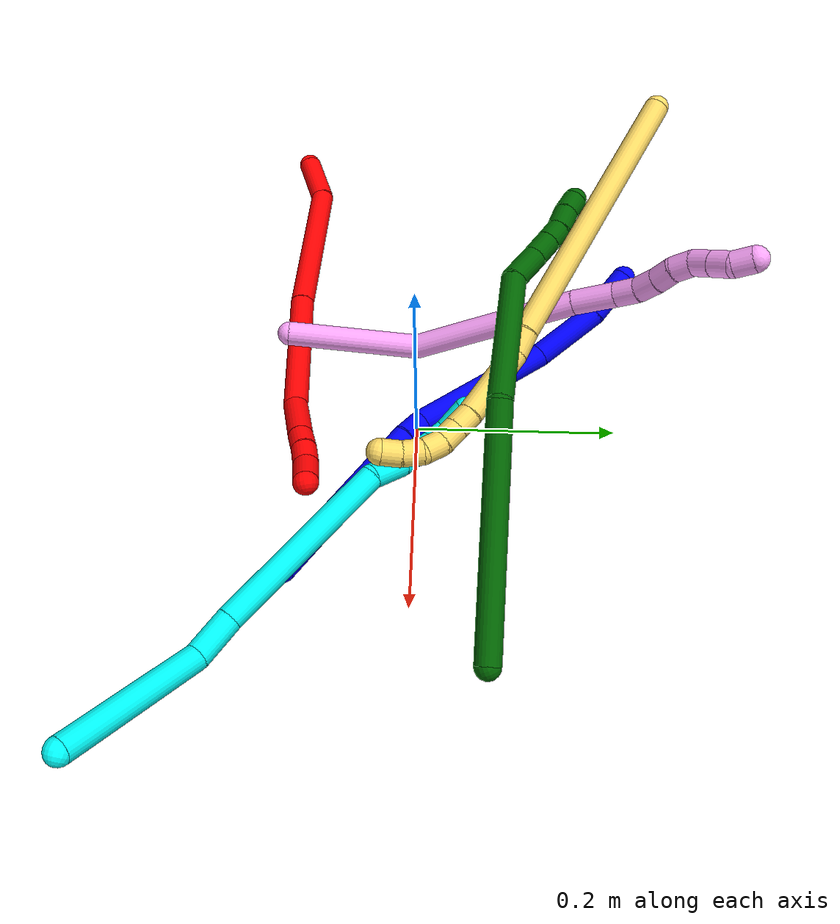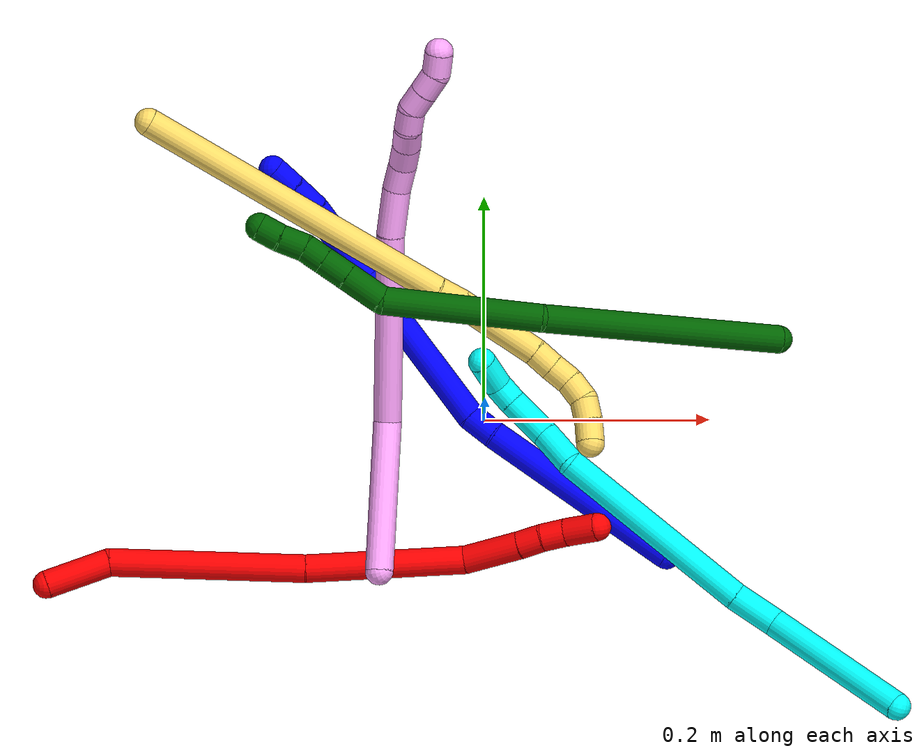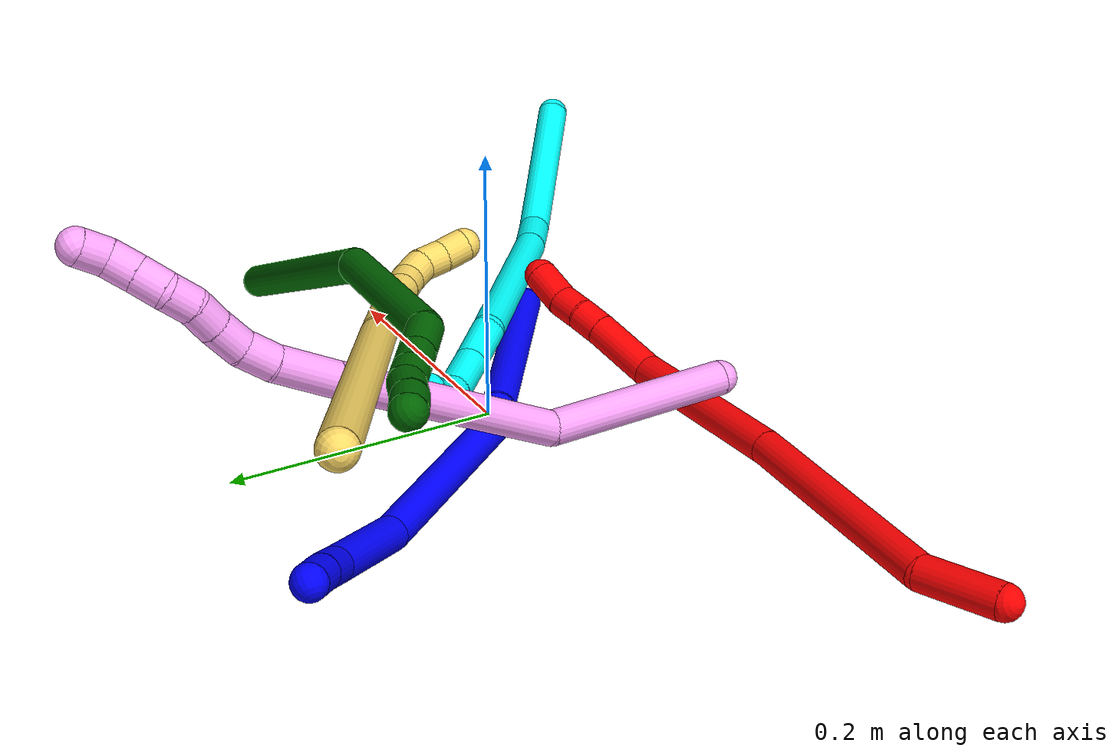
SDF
<sdf version="1.7">
 <world name="default">
  <plugin name="TubeGeneratorPlugin" filename="libtube_generator_plugin.so"/>
  <model name="photoneo_s_sensor">
   <static>1</static>
   <pose>0 0 2 1.57079 1.57079 3.14159</pose>
   <link name="link">
    <inertial><mass>0.1</mass></inertial>
    <sensor name="sensor" type="depth">
     <update_rate>30</update_rate>
     <camera>
      <horizontal_fov>1.22</horizontal_fov>
      <image><width>1920</width><height>1200</height><format>B8G8R8</format></image>
      <clip><near>0.1</near><far>4</far></clip>
      <depth_camera><output>points</output></depth_camera>
     </camera>
     <plugin name="camera_plugin" filename="libgazebo_ros_depth_camera.so">
      <baseline>0.2</baseline>
      <alwaysOn>1</alwaysOn>
      <updateRate>0.0</updateRate>
      <cameraName>camera_ir</cameraName>
      <imageTopicName>/camera/color/image_raw</imageTopicName>
      <cameraInfoTopicName>/camera/color/camera_info</cameraInfoTopicName>
      <depthImageTopicName>/camera/depth/image_raw</depthImageTopicName>
      <depthImageCameraInfoTopicName>/camera/depth/camera_info</depthImageCameraInfoTopicName>
      <pointCloudTopicName>/camera/depth/points</pointCloudTopicName>
      <frameName>fr_optical</frameName>
      <pointCloudCutoff>0.1</pointCloudCutoff>
      <pointCloudCutoffMax>2.0</pointCloudCutoffMax>
      <distortionK1>0</distortionK1>
      <distortionK2>0</distortionK2>
      <distortionK3>0</distortionK3>
      <distortionT1>0</distortionT1>
      <distortionT2>0</distortionT2>
      <CxPrime>0</CxPrime>
      <Cx>0</Cx>
      <Cy>0</Cy>
      <focalLength>0</focalLength>
      <hackBaseline>0</hackBaseline>
     </plugin>
    </sensor>
   </link>
  </model>
  <gravity>0 0 -9.8</gravity>
  <magnetic_field>6e-06 2.3e-05 -4.2e-05</magnetic_field>
  <atmosphere type="adiabatic"/>
  <physics name="default_physics" default="0" type="ode">
   <max_step_size>0.003</max_step_size>
   <real_time_factor>1</real_time_factor>
   <real_time_update_rate>1000</real_time_update_rate>
   <max_contacts>10000</max_contacts>
   <ode>
    <solver>
     <type>quick</type>
     <iters>100</iters>
     <sor>1.3</sor>
     <use_dynamic_moi_rescaling>0</use_dynamic_moi_rescaling>
    </solver>
    <constraints>
     <contact_max_correcting_vel>0</contact_max_correcting_vel>
     <contact_surface_layer>0.001</contact_surface_layer>
     <cfm>0</cfm>
     <erp>0.2</erp>
    </constraints>
   </ode>
  </physics>
  <scene><ambient>0.4 0.4 0.4 1</ambient><background>0.7 0.7 0.7 1</background><shadows>0</shadows></scene>
  <audio><device>default</device></audio>
  <spherical_coordinates>
   <surface_model>EARTH_WGS84</surface_model>
   <latitude_deg>0</latitude_deg>
   <longitude_deg>0</longitude_deg>
   <elevation>0</elevation>
   <heading_deg>0</heading_deg>
  </spherical_coordinates>
  <model name="bin">
   <static>1</static>
   <link name="bottom">
    <collision name="collision-bottom">
     <pose>0 0 -0.01 0 -0 0</pose>
     <geometry><box><size>0.8 0.6 0.02</size></box></geometry>
     <surface>
      <friction><ode><mu>100</mu><mu2>100</mu2></ode></friction>
      <contact><collide_bitmask>65535</collide_bitmask></contact>
     </surface>
    </collision>
   </link>
   <link name="west_wall">
    <collision name="collision-west_wall">
     <pose>-0.41 0 0.1 0 -0 0</pose>
     <geometry><box><size>0.02 0.6 0.2</size></box></geometry>
     <surface>
      <friction><ode><mu>100</mu><mu2>100</mu2></ode></friction>
      <contact><collide_bitmask>65535</collide_bitmask></contact>
     </surface>
    </collision>
   </link>
   <link name="east_wall">
    <collision name="collision-east_wall">
     <pose>0.41 0 0.1 0 -0 0</pose>
     <geometry><box><size>0.02 0.6 0.2</size></box></geometry>
     <surface>
      <friction><ode><mu>100</mu><mu2>100</mu2></ode></friction>
      <contact><collide_bitmask>65535</collide_bitmask></contact>
     </surface>
    </collision>
   </link>
   <link name="south_wall">
    <collision name="collision-south_wall">
     <pose>0 -0.31 0.1 0 -0 0</pose>
     <geometry><box><size>0.8 0.02 0.2</size></box></geometry>
     <surface>
      <friction><ode><mu>100</mu><mu2>100</mu2></ode></friction>
      <contact><collide_bitmask>65535</collide_bitmask></contact>
     </surface>
    </collision>
   </link>
   <link name="north_wall">
    <collision name="collision-north_wall">
     <pose>0 0.31 0.1 0 -0 0</pose>
     <geometry><box><size>0.8 0.02 0.2</size></box></geometry>
     <surface>
      <friction><ode><mu>100</mu><mu2>100</mu2></ode></friction>
      <contact><collide_bitmask>65535</collide_bitmask></contact>
     </surface>
    </collision>
   </link>
  </model>
  <model name="1">
   <static>0</static>
   <link name="1">
    <collision name="collision-cylinder-e_1_1_4">
     <pose>-0.055642 0.040038 -0.063313 -2.57771 -0.638863 1.70309</pose>
     <geometry><cylinder><radius>0.0125</radius><length>0.186628</length></cylinder></geometry>
     <surface>
      <friction><ode><mu>1.16</mu><mu2>1.16</mu2><slip1>0</slip1><slip2>0</slip2></ode></friction>
      <contact><ode><kp>1e+06</kp><kd>1</kd><max_vel>0</max_vel><min_depth>0.001</min_depth></ode></contact>
     </surface>
    </collision>
    <visual name="visual-cylinder-e_1_1_4">
     <pose>-0.055642 0.040038 -0.063313 -2.57771 -0.638863 1.70309</pose>
     <geometry><cylinder><radius>0.0125</radius><length>0.186628</length></cylinder></geometry>
     <material><ambient>0 0 1 1</ambient></material>
    </visual>
    <collision name="collision-cylinder-e_2_4_5">
     <pose>-0.117568 0.086793 -0.136397 -2.53925 -0.487395 1.35005</pose>
     <geometry><cylinder><radius>0.0125</radius><length>0.026841</length></cylinder></geometry>
     <surface>
      <friction><ode><mu>1.16</mu><mu2>1.16</mu2><slip1>0</slip1><slip2>0</slip2></ode></friction>
      <contact><ode><kp>1e+06</kp><kd>1</kd><max_vel>0</max_vel><min_depth>0.001</min_depth></ode></contact>
     </surface>
    </collision>
    <visual name="visual-cylinder-e_2_4_5">
     <pose>-0.117568 0.086793 -0.136397 -2.53925 -0.487395 1.35005</pose>
     <geometry><cylinder><radius>0.0125</radius><length>0.026841</length></cylinder></geometry>
     <material><ambient>0 0 1 1</ambient></material>
    </visual>
    <collision name="collision-cylinder-e_3_5_6">
     <pose>-0.162953 0.147349 -0.187158 -2.22154 -0.523967 0.992094</pose>
     <geometry><cylinder><radius>0.0125</radius><length>0.1563</length></cylinder></geometry>
     <surface>
      <friction><ode><mu>1.16</mu><mu2>1.16</mu2><slip1>0</slip1><slip2>0</slip2></ode></friction>
      <contact><ode><kp>1e+06</kp><kd>1</kd><max_vel>0</max_vel><min_depth>0.001</min_depth></ode></contact>
     </surface>
    </collision>
    <visual name="visual-cylinder-e_3_5_6">
     <pose>-0.162953 0.147349 -0.187158 -2.22154 -0.523967 0.992094</pose>
     <geometry><cylinder><radius>0.0125</radius><length>0.1563</length></cylinder></geometry>
     <material><ambient>0 0 1 1</ambient></material>
    </visual>
    <collision name="collision-cylinder-e_4_6_7">
     <pose>-0.228575 0.225298 -0.242267 -2.10053 -0.759324 1.21613</pose>
     <geometry><cylinder><radius>0.0125</radius><length>0.077049</length></cylinder></geometry>
     <surface>
      <friction><ode><mu>1.16</mu><mu2>1.16</mu2><slip1>0</slip1><slip2>0</slip2></ode></friction>
      <contact><ode><kp>1e+06</kp><kd>1</kd><max_vel>0</max_vel><min_depth>0.001</min_depth></ode></contact>
     </surface>
    </collision>
    <visual name="visual-cylinder-e_4_6_7">
     <pose>-0.228575 0.225298 -0.242267 -2.10053 -0.759324 1.21613</pose>
     <geometry><cylinder><radius>0.0125</radius><length>0.077049</length></cylinder></geometry>
     <material><ambient>0 0 1 1</ambient></material>
    </visual>
    <collision name="collision-cylinder-e_5_7_8">
     <pose>-0.267094 0.255654 -0.261637 -2.2701 -0.973602 1.69867</pose>
     <geometry><cylinder><radius>0.0125</radius><length>0.029018</length></cylinder></geometry>
     <surface>
      <friction><ode><mu>1.16</mu><mu2>1.16</mu2><slip1>0</slip1><slip2>0</slip2></ode></friction>
      <contact><ode><kp>1e+06</kp><kd>1</kd><max_vel>0</max_vel><min_depth>0.001</min_depth></ode></contact>
     </surface>
    </collision>
    <visual name="visual-cylinder-e_5_7_8">
     <pose>-0.267094 0.255654 -0.261637 -2.2701 -0.973602 1.69867</pose>
     <geometry><cylinder><radius>0.0125</radius><length>0.029018</length></cylinder></geometry>
     <material><ambient>0 0 1 1</ambient></material>
    </visual>
    <collision name="collision-cylinder-e_6_8_2">
     <pose>-0.28866 0.267225 -0.271994 -2.33487 -0.913916 1.7119</pose>
     <geometry><cylinder><radius>0.0125</radius><length>0.024164</length></cylinder></geometry>
     <surface>
      <friction><ode><mu>1.16</mu><mu2>1.16</mu2><slip1>0</slip1><slip2>0</slip2></ode></friction>
      <contact><ode><kp>1e+06</kp><kd>1</kd><max_vel>0</max_vel><min_depth>0.001</min_depth></ode></contact>
     </surface>
    </collision>
    <visual name="visual-cylinder-e_6_8_2">
     <pose>-0.28866 0.267225 -0.271994 -2.33487 -0.913916 1.7119</pose>
     <geometry><cylinder><radius>0.0125</radius><length>0.024164</length></cylinder></geometry>
     <material><ambient>0 0 1 1</ambient></material>
    </visual>
    <collision name="collision-sphere-2">
     <pose>-0.298227 0.272552 -0.277098 0 -0 0</pose>
     <geometry><sphere><radius>0.0125</radius></sphere></geometry>
     <surface>
      <friction><ode><mu>1.16</mu><mu2>1.16</mu2><slip1>0</slip1><slip2>0</slip2></ode></friction>
      <contact><ode><kp>1e+06</kp><kd>1</kd><max_vel>0</max_vel><min_depth>0.001</min_depth></ode></contact>
     </surface>
    </collision>
    <visual name="visual-sphere-2">
     <pose>-0.298227 0.272552 -0.277098 0 -0 0</pose>
     <geometry><sphere><radius>0.0125</radius></sphere></geometry>
     <material><ambient>0 0 1 1</ambient></material>
    </visual>
    <collision name="collision-sphere-4">
     <pose>-0.111283 0.080075 -0.126626 0 -0 0</pose>
     <geometry><sphere><radius>0.0125</radius></sphere></geometry>
     <surface>
      <friction><ode><mu>1.16</mu><mu2>1.16</mu2><slip1>0</slip1><slip2>0</slip2></ode></friction>
      <contact><ode><kp>1e+06</kp><kd>1</kd><max_vel>0</max_vel><min_depth>0.001</min_depth></ode></contact>
     </surface>
    </collision>
    <visual name="visual-sphere-4">
     <pose>-0.111283 0.080075 -0.126626 0 -0 0</pose>
     <geometry><sphere><radius>0.0125</radius></sphere></geometry>
     <material><ambient>0 0 1 1</ambient></material>
    </visual>
    <collision name="collision-sphere-1">
     <geometry><sphere><radius>0.0125</radius></sphere></geometry>
     <surface>
      <friction><ode><mu>1.16</mu><mu2>1.16</mu2><slip1>0</slip1><slip2>0</slip2></ode></friction>
      <contact><ode><kp>1e+06</kp><kd>1</kd><max_vel>0</max_vel><min_depth>0.001</min_depth></ode></contact>
     </surface>
    </collision>
    <visual name="visual-sphere-1">
     <geometry><sphere><radius>0.0125</radius></sphere></geometry>
     <material><ambient>0 0 1 1</ambient></material>
    </visual>
    <collision name="collision-sphere-8">
     <pose>-0.279092 0.261898 -0.266889 0 -0 0</pose>
     <geometry><sphere><radius>0.0125</radius></sphere></geometry>
     <surface>
      <friction><ode><mu>1.16</mu><mu2>1.16</mu2><slip1>0</slip1><slip2>0</slip2></ode></friction>
      <contact><ode><kp>1e+06</kp><kd>1</kd><max_vel>0</max_vel><min_depth>0.001</min_depth></ode></contact>
     </surface>
    </collision>
    <visual name="visual-sphere-8">
     <pose>-0.279092 0.261898 -0.266889 0 -0 0</pose>
     <geometry><sphere><radius>0.0125</radius></sphere></geometry>
     <material><ambient>0 0 1 1</ambient></material>
    </visual>
    <collision name="collision-sphere-5">
     <pose>-0.123854 0.093512 -0.146168 0 -0 0</pose>
     <geometry><sphere><radius>0.0125</radius></sphere></geometry>
     <surface>
      <friction><ode><mu>1.16</mu><mu2>1.16</mu2><slip1>0</slip1><slip2>0</slip2></ode></friction>
      <contact><ode><kp>1e+06</kp><kd>1</kd><max_vel>0</max_vel><min_depth>0.001</min_depth></ode></contact>
     </surface>
    </collision>
    <visual name="visual-sphere-5">
     <pose>-0.123854 0.093512 -0.146168 0 -0 0</pose>
     <geometry><sphere><radius>0.0125</radius></sphere></geometry>
     <material><ambient>0 0 1 1</ambient></material>
    </visual>
    <collision name="collision-sphere-6">
     <pose>-0.202053 0.201186 -0.228148 0 -0 0</pose>
     <geometry><sphere><radius>0.0125</radius></sphere></geometry>
     <surface>
      <friction><ode><mu>1.16</mu><mu2>1.16</mu2><slip1>0</slip1><slip2>0</slip2></ode></friction>
      <contact><ode><kp>1e+06</kp><kd>1</kd><max_vel>0</max_vel><min_depth>0.001</min_depth></ode></contact>
     </surface>
    </collision>
    <visual name="visual-sphere-6">
     <pose>-0.202053 0.201186 -0.228148 0 -0 0</pose>
     <geometry><sphere><radius>0.0125</radius></sphere></geometry>
     <material><ambient>0 0 1 1</ambient></material>
    </visual>
    <collision name="collision-sphere-7">
     <pose>-0.255096 0.24941 -0.256386 0 -0 0</pose>
     <geometry><sphere><radius>0.0125</radius></sphere></geometry>
     <surface>
      <friction><ode><mu>1.16</mu><mu2>1.16</mu2><slip1>0</slip1><slip2>0</slip2></ode></friction>
      <contact><ode><kp>1e+06</kp><kd>1</kd><max_vel>0</max_vel><min_depth>0.001</min_depth></ode></contact>
     </surface>
    </collision>
    <visual name="visual-sphere-7">
     <pose>-0.255096 0.24941 -0.256386 0 -0 0</pose>
     <geometry><sphere><radius>0.0125</radius></sphere></geometry>
     <material><ambient>0 0 1 1</ambient></material>
    </visual>
    <inertial>
     <pose>-0.142693 0.128134 -0.155122 0 -0 0</pose>
     <mass>0.5</mass>
     <inertia>
      <ixx>0.000788</ixx>
      <ixy>0</ixy>
      <ixz>0</ixz>
      <iyy>0.000981</iyy>
      <iyz>0</iyz>
      <izz>1.3e-05</izz>
     </inertia>
    </inertial>
   </link>
   <pose>0.161494 -0.120119 -0.005364 -0.249536 0.93156 -0.362237</pose>
  </model>
  <model name="2">
   <static>0</static>
   <link name="2">
    <collision name="collision-cylinder-e_1_1_4">
     <pose>0.009213 0.007219 -0.026918 -2.87956 0.319256 -1.7698</pose>
     <geometry><cylinder><radius>0.0125</radius><length>0.058705</length></cylinder></geometry>
     <surface>
      <friction><ode><mu>1.16</mu><mu2>1.16</mu2><slip1>0</slip1><slip2>0</slip2></ode></friction>
      <contact><ode><kp>1e+06</kp><kd>1</kd><max_vel>0</max_vel><min_depth>0.001</min_depth></ode></contact>
     </surface>
    </collision>
    <visual name="visual-cylinder-e_1_1_4">
     <pose>0.009213 0.007219 -0.026918 -2.87956 0.319256 -1.7698</pose>
     <geometry><cylinder><radius>0.0125</radius><length>0.058705</length></cylinder></geometry>
     <material><ambient>1 0 0 1</ambient></material>
    </visual>
    <collision name="collision-cylinder-e_2_4_5">
     <pose>0.062412 0.007383 -0.128678 3.0476 0.529418 2.79802</pose>
     <geometry><cylinder><radius>0.0125</radius><length>0.174195</length></cylinder></geometry>
     <surface>
      <friction><ode><mu>1.16</mu><mu2>1.16</mu2><slip1>0</slip1><slip2>0</slip2></ode></friction>
      <contact><ode><kp>1e+06</kp><kd>1</kd><max_vel>0</max_vel><min_depth>0.001</min_depth></ode></contact>
     </surface>
    </collision>
    <visual name="visual-cylinder-e_2_4_5">
     <pose>0.062412 0.007383 -0.128678 3.0476 0.529418 2.79802</pose>
     <geometry><cylinder><radius>0.0125</radius><length>0.174195</length></cylinder></geometry>
     <material><ambient>1 0 0 1</ambient></material>
    </visual>
    <collision name="collision-cylinder-e_3_5_6">
     <pose>0.138967 -0.0001 -0.266398 3.13479 0.477902 3.11367</pose>
     <geometry><cylinder><radius>0.0125</radius><length>0.141627</length></cylinder></geometry>
     <surface>
      <friction><ode><mu>1.16</mu><mu2>1.16</mu2><slip1>0</slip1><slip2>0</slip2></ode></friction>
      <contact><ode><kp>1e+06</kp><kd>1</kd><max_vel>0</max_vel><min_depth>0.001</min_depth></ode></contact>
     </surface>
    </collision>
    <visual name="visual-cylinder-e_3_5_6">
     <pose>0.138967 -0.0001 -0.266398 3.13479 0.477902 3.11367</pose>
     <geometry><cylinder><radius>0.0125</radius><length>0.141627</length></cylinder></geometry>
     <material><ambient>1 0 0 1</ambient></material>
    </visual>
    <collision name="collision-cylinder-e_4_6_7">
     <pose>0.188359 0.006488 -0.348212 -2.78677 0.694587 -2.22175</pose>
     <geometry><cylinder><radius>0.0125</radius><length>0.052565</length></cylinder></geometry>
     <surface>
      <friction><ode><mu>1.16</mu><mu2>1.16</mu2><slip1>0</slip1><slip2>0</slip2></ode></friction>
      <contact><ode><kp>1e+06</kp><kd>1</kd><max_vel>0</max_vel><min_depth>0.001</min_depth></ode></contact>
     </surface>
    </collision>
    <visual name="visual-cylinder-e_4_6_7">
     <pose>0.188359 0.006488 -0.348212 -2.78677 0.694587 -2.22175</pose>
     <geometry><cylinder><radius>0.0125</radius><length>0.052565</length></cylinder></geometry>
     <material><ambient>1 0 0 1</ambient></material>
    </visual>
    <collision name="collision-cylinder-e_5_7_8">
     <pose>0.21163 0.01679 -0.374954 -2.74314 0.650783 -2.06304</pose>
     <geometry><cylinder><radius>0.0125</radius><length>0.02129</length></cylinder></geometry>
     <surface>
      <friction><ode><mu>1.16</mu><mu2>1.16</mu2><slip1>0</slip1><slip2>0</slip2></ode></friction>
      <contact><ode><kp>1e+06</kp><kd>1</kd><max_vel>0</max_vel><min_depth>0.001</min_depth></ode></contact>
     </surface>
    </collision>
    <visual name="visual-cylinder-e_5_7_8">
     <pose>0.21163 0.01679 -0.374954 -2.74314 0.650783 -2.06304</pose>
     <geometry><cylinder><radius>0.0125</radius><length>0.02129</length></cylinder></geometry>
     <material><ambient>1 0 0 1</ambient></material>
    </visual>
    <collision name="collision-cylinder-e_6_8_9">
     <pose>0.224182 0.022308 -0.391518 -2.89214 0.593936 -2.36391</pose>
     <geometry><cylinder><radius>0.0125</radius><length>0.021812</length></cylinder></geometry>
     <surface>
      <friction><ode><mu>1.16</mu><mu2>1.16</mu2><slip1>0</slip1><slip2>0</slip2></ode></friction>
      <contact><ode><kp>1e+06</kp><kd>1</kd><max_vel>0</max_vel><min_depth>0.001</min_depth></ode></contact>
     </surface>
    </collision>
    <visual name="visual-cylinder-e_6_8_9">
     <pose>0.224182 0.022308 -0.391518 -2.89214 0.593936 -2.36391</pose>
     <geometry><cylinder><radius>0.0125</radius><length>0.021812</length></cylinder></geometry>
     <material><ambient>1 0 0 1</ambient></material>
    </visual>
    <collision name="collision-cylinder-e_7_9_2">
     <pose>0.241149 0.027547 -0.410024 -2.84225 0.816814 -2.47097</pose>
     <geometry><cylinder><radius>0.0125</radius><length>0.029806</length></cylinder></geometry>
     <surface>
      <friction><ode><mu>1.16</mu><mu2>1.16</mu2><slip1>0</slip1><slip2>0</slip2></ode></friction>
      <contact><ode><kp>1e+06</kp><kd>1</kd><max_vel>0</max_vel><min_depth>0.001</min_depth></ode></contact>
     </surface>
    </collision>
    <visual name="visual-cylinder-e_7_9_2">
     <pose>0.241149 0.027547 -0.410024 -2.84225 0.816814 -2.47097</pose>
     <geometry><cylinder><radius>0.0125</radius><length>0.029806</length></cylinder></geometry>
     <material><ambient>1 0 0 1</ambient></material>
    </visual>
    <collision name="collision-sphere-2">
     <pose>0.252013 0.030556 -0.419772 0 -0 0</pose>
     <geometry><sphere><radius>0.0125</radius></sphere></geometry>
     <surface>
      <friction><ode><mu>1.16</mu><mu2>1.16</mu2><slip1>0</slip1><slip2>0</slip2></ode></friction>
      <contact><ode><kp>1e+06</kp><kd>1</kd><max_vel>0</max_vel><min_depth>0.001</min_depth></ode></contact>
     </surface>
    </collision>
    <visual name="visual-sphere-2">
     <pose>0.252013 0.030556 -0.419772 0 -0 0</pose>
     <geometry><sphere><radius>0.0125</radius></sphere></geometry>
     <material><ambient>1 0 0 1</ambient></material>
    </visual>
    <collision name="collision-sphere-9">
     <pose>0.230286 0.024539 -0.400276 0 -0 0</pose>
     <geometry><sphere><radius>0.0125</radius></sphere></geometry>
     <surface>
      <friction><ode><mu>1.16</mu><mu2>1.16</mu2><slip1>0</slip1><slip2>0</slip2></ode></friction>
      <contact><ode><kp>1e+06</kp><kd>1</kd><max_vel>0</max_vel><min_depth>0.001</min_depth></ode></contact>
     </surface>
    </collision>
    <visual name="visual-sphere-9">
     <pose>0.230286 0.024539 -0.400276 0 -0 0</pose>
     <geometry><sphere><radius>0.0125</radius></sphere></geometry>
     <material><ambient>1 0 0 1</ambient></material>
    </visual>
    <collision name="collision-sphere-4">
     <pose>0.018425 0.014439 -0.053836 0 -0 0</pose>
     <geometry><sphere><radius>0.0125</radius></sphere></geometry>
     <surface>
      <friction><ode><mu>1.16</mu><mu2>1.16</mu2><slip1>0</slip1><slip2>0</slip2></ode></friction>
      <contact><ode><kp>1e+06</kp><kd>1</kd><max_vel>0</max_vel><min_depth>0.001</min_depth></ode></contact>
     </surface>
    </collision>
    <visual name="visual-sphere-4">
     <pose>0.018425 0.014439 -0.053836 0 -0 0</pose>
     <geometry><sphere><radius>0.0125</radius></sphere></geometry>
     <material><ambient>1 0 0 1</ambient></material>
    </visual>
    <collision name="collision-sphere-1">
     <geometry><sphere><radius>0.0125</radius></sphere></geometry>
     <surface>
      <friction><ode><mu>1.16</mu><mu2>1.16</mu2><slip1>0</slip1><slip2>0</slip2></ode></friction>
      <contact><ode><kp>1e+06</kp><kd>1</kd><max_vel>0</max_vel><min_depth>0.001</min_depth></ode></contact>
     </surface>
    </collision>
    <visual name="visual-sphere-1">
     <geometry><sphere><radius>0.0125</radius></sphere></geometry>
     <material><ambient>1 0 0 1</ambient></material>
    </visual>
    <collision name="collision-sphere-8">
     <pose>0.218079 0.020076 -0.38276 0 -0 0</pose>
     <geometry><sphere><radius>0.0125</radius></sphere></geometry>
     <surface>
      <friction><ode><mu>1.16</mu><mu2>1.16</mu2><slip1>0</slip1><slip2>0</slip2></ode></friction>
      <contact><ode><kp>1e+06</kp><kd>1</kd><max_vel>0</max_vel><min_depth>0.001</min_depth></ode></contact>
     </surface>
    </collision>
    <visual name="visual-sphere-8">
     <pose>0.218079 0.020076 -0.38276 0 -0 0</pose>
     <geometry><sphere><radius>0.0125</radius></sphere></geometry>
     <material><ambient>1 0 0 1</ambient></material>
    </visual>
    <collision name="collision-sphere-5">
     <pose>0.106399 0.000328 -0.20352 0 -0 0</pose>
     <geometry><sphere><radius>0.0125</radius></sphere></geometry>
     <surface>
      <friction><ode><mu>1.16</mu><mu2>1.16</mu2><slip1>0</slip1><slip2>0</slip2></ode></friction>
      <contact><ode><kp>1e+06</kp><kd>1</kd><max_vel>0</max_vel><min_depth>0.001</min_depth></ode></contact>
     </surface>
    </collision>
    <visual name="visual-sphere-5">
     <pose>0.106399 0.000328 -0.20352 0 -0 0</pose>
     <geometry><sphere><radius>0.0125</radius></sphere></geometry>
     <material><ambient>1 0 0 1</ambient></material>
    </visual>
    <collision name="collision-sphere-6">
     <pose>0.171536 -0.000527 -0.329277 0 -0 0</pose>
     <geometry><sphere><radius>0.0125</radius></sphere></geometry>
     <surface>
      <friction><ode><mu>1.16</mu><mu2>1.16</mu2><slip1>0</slip1><slip2>0</slip2></ode></friction>
      <contact><ode><kp>1e+06</kp><kd>1</kd><max_vel>0</max_vel><min_depth>0.001</min_depth></ode></contact>
     </surface>
    </collision>
    <visual name="visual-sphere-6">
     <pose>0.171536 -0.000527 -0.329277 0 -0 0</pose>
     <geometry><sphere><radius>0.0125</radius></sphere></geometry>
     <material><ambient>1 0 0 1</ambient></material>
    </visual>
    <collision name="collision-sphere-7">
     <pose>0.205181 0.013504 -0.367148 0 -0 0</pose>
     <geometry><sphere><radius>0.0125</radius></sphere></geometry>
     <surface>
      <friction><ode><mu>1.16</mu><mu2>1.16</mu2><slip1>0</slip1><slip2>0</slip2></ode></friction>
      <contact><ode><kp>1e+06</kp><kd>1</kd><max_vel>0</max_vel><min_depth>0.001</min_depth></ode></contact>
     </surface>
    </collision>
    <visual name="visual-sphere-7">
     <pose>0.205181 0.013504 -0.367148 0 -0 0</pose>
     <geometry><sphere><radius>0.0125</radius></sphere></geometry>
     <material><ambient>1 0 0 1</ambient></material>
    </visual>
    <inertial>
     <pose>0.115157 0.007404 -0.217544 0 -0 0</pose>
     <mass>0.5</mass>
     <inertia>
      <ixx>-0.000466</ixx>
      <ixy>0</ixy>
      <ixz>0</ixz>
      <iyy>0.000798</iyy>
      <iyz>0</iyz>
      <izz>-0.000362</izz>
     </inertia>
    </inertial>
   </link>
   <pose>-0.388089 -0.146341 0.014939 0.67056 -0.973482 -0.525258</pose>
  </model>
  <model name="3">
   <static>0</static>
   <link name="3">
    <collision name="collision-cylinder-e_1_1_4">
     <pose>0.045143 0.032458 -0.044565 -2.51211 0.68611 -1.66333</pose>
     <geometry><cylinder><radius>0.0125</radius><length>0.142513</length></cylinder></geometry>
     <surface>
      <friction><ode><mu>1.16</mu><mu2>1.16</mu2><slip1>0</slip1><slip2>0</slip2></ode></friction>
      <contact><ode><kp>1e+06</kp><kd>1</kd><max_vel>0</max_vel><min_depth>0.001</min_depth></ode></contact>
     </surface>
    </collision>
    <visual name="visual-cylinder-e_1_1_4">
     <pose>0.045143 0.032458 -0.044565 -2.51211 0.68611 -1.66333</pose>
     <geometry><cylinder><radius>0.0125</radius><length>0.142513</length></cylinder></geometry>
     <material><ambient>0.003922 1 0.996078 1</ambient></material>
    </visual>
    <collision name="collision-cylinder-e_2_4_5">
     <pose>0.095356 0.073518 -0.10804 -2.71467 0.239338 -1.01293</pose>
     <geometry><cylinder><radius>0.0125</radius><length>0.042767</length></cylinder></geometry>
     <surface>
      <friction><ode><mu>1.16</mu><mu2>1.16</mu2><slip1>0</slip1><slip2>0</slip2></ode></friction>
      <contact><ode><kp>1e+06</kp><kd>1</kd><max_vel>0</max_vel><min_depth>0.001</min_depth></ode></contact>
     </surface>
    </collision>
    <visual name="visual-cylinder-e_2_4_5">
     <pose>0.095356 0.073518 -0.10804 -2.71467 0.239338 -1.01293</pose>
     <geometry><cylinder><radius>0.0125</radius><length>0.042767</length></cylinder></geometry>
     <material><ambient>0.003922 1 0.996078 1</ambient></material>
    </visual>
    <collision name="collision-cylinder-e_3_5_6">
     <pose>0.119198 0.126822 -0.206965 -2.63212 0.202021 -0.742392</pose>
     <geometry><cylinder><radius>0.0125</radius><length>0.187118</length></cylinder></geometry>
     <surface>
      <friction><ode><mu>1.16</mu><mu2>1.16</mu2><slip1>0</slip1><slip2>0</slip2></ode></friction>
      <contact><ode><kp>1e+06</kp><kd>1</kd><max_vel>0</max_vel><min_depth>0.001</min_depth></ode></contact>
     </surface>
    </collision>
    <visual name="visual-cylinder-e_3_5_6">
     <pose>0.119198 0.126822 -0.206965 -2.63212 0.202021 -0.742392</pose>
     <geometry><cylinder><radius>0.0125</radius><length>0.187118</length></cylinder></geometry>
     <material><ambient>0.003922 1 0.996078 1</ambient></material>
    </visual>
    <collision name="collision-cylinder-e_4_6_7">
     <pose>0.146616 0.183367 -0.297833 -2.31256 0.49378 -1.04033</pose>
     <geometry><cylinder><radius>0.0125</radius><length>0.036484</length></cylinder></geometry>
     <surface>
      <friction><ode><mu>1.16</mu><mu2>1.16</mu2><slip1>0</slip1><slip2>0</slip2></ode></friction>
      <contact><ode><kp>1e+06</kp><kd>1</kd><max_vel>0</max_vel><min_depth>0.001</min_depth></ode></contact>
     </surface>
    </collision>
    <visual name="visual-cylinder-e_4_6_7">
     <pose>0.146616 0.183367 -0.297833 -2.31256 0.49378 -1.04033</pose>
     <geometry><cylinder><radius>0.0125</radius><length>0.036484</length></cylinder></geometry>
     <material><ambient>0.003922 1 0.996078 1</ambient></material>
    </visual>
    <collision name="collision-cylinder-e_5_7_8">
     <pose>0.161739 0.207269 -0.324064 -2.47662 0.320022 -0.87444</pose>
     <geometry><cylinder><radius>0.0125</radius><length>0.041176</length></cylinder></geometry>
     <surface>
      <friction><ode><mu>1.16</mu><mu2>1.16</mu2><slip1>0</slip1><slip2>0</slip2></ode></friction>
      <contact><ode><kp>1e+06</kp><kd>1</kd><max_vel>0</max_vel><min_depth>0.001</min_depth></ode></contact>
     </surface>
    </collision>
    <visual name="visual-cylinder-e_5_7_8">
     <pose>0.161739 0.207269 -0.324064 -2.47662 0.320022 -0.87444</pose>
     <geometry><cylinder><radius>0.0125</radius><length>0.041176</length></cylinder></geometry>
     <material><ambient>0.003922 1 0.996078 1</ambient></material>
    </visual>
    <collision name="collision-cylinder-e_6_8_9">
     <pose>0.168836 0.225348 -0.347479 -2.49863 0.061696 -0.184786</pose>
     <geometry><cylinder><radius>0.0125</radius><length>0.020121</length></cylinder></geometry>
     <surface>
      <friction><ode><mu>1.16</mu><mu2>1.16</mu2><slip1>0</slip1><slip2>0</slip2></ode></friction>
      <contact><ode><kp>1e+06</kp><kd>1</kd><max_vel>0</max_vel><min_depth>0.001</min_depth></ode></contact>
     </surface>
    </collision>
    <visual name="visual-cylinder-e_6_8_9">
     <pose>0.168836 0.225348 -0.347479 -2.49863 0.061696 -0.184786</pose>
     <geometry><cylinder><radius>0.0125</radius><length>0.020121</length></cylinder></geometry>
     <material><ambient>0.003922 1 0.996078 1</ambient></material>
    </visual>
    <collision name="collision-cylinder-e_7_9_2">
     <pose>0.1631 0.238511 -0.366957 -2.58353 -0.440364 1.32631</pose>
     <geometry><cylinder><radius>0.0125</radius><length>0.029821</length></cylinder></geometry>
     <surface>
      <friction><ode><mu>1.16</mu><mu2>1.16</mu2><slip1>0</slip1><slip2>0</slip2></ode></friction>
      <contact><ode><kp>1e+06</kp><kd>1</kd><max_vel>0</max_vel><min_depth>0.001</min_depth></ode></contact>
     </surface>
    </collision>
    <visual name="visual-cylinder-e_7_9_2">
     <pose>0.1631 0.238511 -0.366957 -2.58353 -0.440364 1.32631</pose>
     <geometry><cylinder><radius>0.0125</radius><length>0.029821</length></cylinder></geometry>
     <material><ambient>0.003922 1 0.996078 1</ambient></material>
    </visual>
    <collision name="collision-sphere-2">
     <pose>0.156744 0.245653 -0.378399 0 -0 0</pose>
     <geometry><sphere><radius>0.0125</radius></sphere></geometry>
     <surface>
      <friction><ode><mu>1.16</mu><mu2>1.16</mu2><slip1>0</slip1><slip2>0</slip2></ode></friction>
      <contact><ode><kp>1e+06</kp><kd>1</kd><max_vel>0</max_vel><min_depth>0.001</min_depth></ode></contact>
     </surface>
    </collision>
    <visual name="visual-sphere-2">
     <pose>0.156744 0.245653 -0.378399 0 -0 0</pose>
     <geometry><sphere><radius>0.0125</radius></sphere></geometry>
     <material><ambient>0.003922 1 0.996078 1</ambient></material>
    </visual>
    <collision name="collision-sphere-9">
     <pose>0.169456 0.231368 -0.355515 0 -0 0</pose>
     <geometry><sphere><radius>0.0125</radius></sphere></geometry>
     <surface>
      <friction><ode><mu>1.16</mu><mu2>1.16</mu2><slip1>0</slip1><slip2>0</slip2></ode></friction>
      <contact><ode><kp>1e+06</kp><kd>1</kd><max_vel>0</max_vel><min_depth>0.001</min_depth></ode></contact>
     </surface>
    </collision>
    <visual name="visual-sphere-9">
     <pose>0.169456 0.231368 -0.355515 0 -0 0</pose>
     <geometry><sphere><radius>0.0125</radius></sphere></geometry>
     <material><ambient>0.003922 1 0.996078 1</ambient></material>
    </visual>
    <collision name="collision-sphere-4">
     <pose>0.090287 0.064916 -0.08913 0 -0 0</pose>
     <geometry><sphere><radius>0.0125</radius></sphere></geometry>
     <surface>
      <friction><ode><mu>1.16</mu><mu2>1.16</mu2><slip1>0</slip1><slip2>0</slip2></ode></friction>
      <contact><ode><kp>1e+06</kp><kd>1</kd><max_vel>0</max_vel><min_depth>0.001</min_depth></ode></contact>
     </surface>
    </collision>
    <visual name="visual-sphere-4">
     <pose>0.090287 0.064916 -0.08913 0 -0 0</pose>
     <geometry><sphere><radius>0.0125</radius></sphere></geometry>
     <material><ambient>0.003922 1 0.996078 1</ambient></material>
    </visual>
    <collision name="collision-sphere-1">
     <geometry><sphere><radius>0.0125</radius></sphere></geometry>
     <surface>
      <friction><ode><mu>1.16</mu><mu2>1.16</mu2><slip1>0</slip1><slip2>0</slip2></ode></friction>
      <contact><ode><kp>1e+06</kp><kd>1</kd><max_vel>0</max_vel><min_depth>0.001</min_depth></ode></contact>
     </surface>
    </collision>
    <visual name="visual-sphere-1">
     <geometry><sphere><radius>0.0125</radius></sphere></geometry>
     <material><ambient>0.003922 1 0.996078 1</ambient></material>
    </visual>
    <collision name="collision-sphere-8">
     <pose>0.168216 0.219327 -0.339443 0 -0 0</pose>
     <geometry><sphere><radius>0.0125</radius></sphere></geometry>
     <surface>
      <friction><ode><mu>1.16</mu><mu2>1.16</mu2><slip1>0</slip1><slip2>0</slip2></ode></friction>
      <contact><ode><kp>1e+06</kp><kd>1</kd><max_vel>0</max_vel><min_depth>0.001</min_depth></ode></contact>
     </surface>
    </collision>
    <visual name="visual-sphere-8">
     <pose>0.168216 0.219327 -0.339443 0 -0 0</pose>
     <geometry><sphere><radius>0.0125</radius></sphere></geometry>
     <material><ambient>0.003922 1 0.996078 1</ambient></material>
    </visual>
    <collision name="collision-sphere-5">
     <pose>0.100425 0.08212 -0.126949 0 -0 0</pose>
     <geometry><sphere><radius>0.0125</radius></sphere></geometry>
     <surface>
      <friction><ode><mu>1.16</mu><mu2>1.16</mu2><slip1>0</slip1><slip2>0</slip2></ode></friction>
      <contact><ode><kp>1e+06</kp><kd>1</kd><max_vel>0</max_vel><min_depth>0.001</min_depth></ode></contact>
     </surface>
    </collision>
    <visual name="visual-sphere-5">
     <pose>0.100425 0.08212 -0.126949 0 -0 0</pose>
     <geometry><sphere><radius>0.0125</radius></sphere></geometry>
     <material><ambient>0.003922 1 0.996078 1</ambient></material>
    </visual>
    <collision name="collision-sphere-6">
     <pose>0.13797 0.171524 -0.286981 0 -0 0</pose>
     <geometry><sphere><radius>0.0125</radius></sphere></geometry>
     <surface>
      <friction><ode><mu>1.16</mu><mu2>1.16</mu2><slip1>0</slip1><slip2>0</slip2></ode></friction>
      <contact><ode><kp>1e+06</kp><kd>1</kd><max_vel>0</max_vel><min_depth>0.001</min_depth></ode></contact>
     </surface>
    </collision>
    <visual name="visual-sphere-6">
     <pose>0.13797 0.171524 -0.286981 0 -0 0</pose>
     <geometry><sphere><radius>0.0125</radius></sphere></geometry>
     <material><ambient>0.003922 1 0.996078 1</ambient></material>
    </visual>
    <collision name="collision-sphere-7">
     <pose>0.155262 0.19521 -0.308685 0 -0 0</pose>
     <geometry><sphere><radius>0.0125</radius></sphere></geometry>
     <surface>
      <friction><ode><mu>1.16</mu><mu2>1.16</mu2><slip1>0</slip1><slip2>0</slip2></ode></friction>
      <contact><ode><kp>1e+06</kp><kd>1</kd><max_vel>0</max_vel><min_depth>0.001</min_depth></ode></contact>
     </surface>
    </collision>
    <visual name="visual-sphere-7">
     <pose>0.155262 0.19521 -0.308685 0 -0 0</pose>
     <geometry><sphere><radius>0.0125</radius></sphere></geometry>
     <material><ambient>0.003922 1 0.996078 1</ambient></material>
    </visual>
    <inertial>
     <pose>0.106171 0.116744 -0.183686 0 -0 0</pose>
     <mass>0.5</mass>
     <inertia>
      <ixx>-0.000163</ixx>
      <ixy>0</ixy>
      <ixz>0</ixz>
      <iyy>-0.000767</iyy>
      <iyz>0</iyz>
      <izz>-0.000693</izz>
     </inertia>
    </inertial>
   </link>
   <pose>0.360623 -0.259683 0.070685 -2.85995 1.19502 -3.04831</pose>
  </model>
  <model name="4">
   <static>0</static>
   <link name="4">
    <collision name="collision-cylinder-e_1_1_4">
     <pose>0.023249 0.062705 0.006653 -1.4651 0.35324 -0.318374</pose>
     <geometry><cylinder><radius>0.0125</radius><length>0.134413</length></cylinder></geometry>
     <surface>
      <friction><ode><mu>1.16</mu><mu2>1.16</mu2><slip1>0</slip1><slip2>0</slip2></ode></friction>
      <contact><ode><kp>1e+06</kp><kd>1</kd><max_vel>0</max_vel><min_depth>0.001</min_depth></ode></contact>
     </surface>
    </collision>
    <visual name="visual-cylinder-e_1_1_4">
     <pose>0.023249 0.062705 0.006653 -1.4651 0.35324 -0.318374</pose>
     <geometry><cylinder><radius>0.0125</radius><length>0.134413</length></cylinder></geometry>
     <material><ambient>1 0.65098 0.996078 1</ambient></material>
    </visual>
    <collision name="collision-cylinder-e_2_4_5">
     <pose>0.037279 0.206842 0.042992 -1.22121 -0.105974 0.074198</pose>
     <geometry><cylinder><radius>0.0125</radius><length>0.174328</length></cylinder></geometry>
     <surface>
      <friction><ode><mu>1.16</mu><mu2>1.16</mu2><slip1>0</slip1><slip2>0</slip2></ode></friction>
      <contact><ode><kp>1e+06</kp><kd>1</kd><max_vel>0</max_vel><min_depth>0.001</min_depth></ode></contact>
     </surface>
    </collision>
    <visual name="visual-cylinder-e_2_4_5">
     <pose>0.037279 0.206842 0.042992 -1.22121 -0.105974 0.074198</pose>
     <geometry><cylinder><radius>0.0125</radius><length>0.174328</length></cylinder></geometry>
     <material><ambient>1 0.65098 0.996078 1</ambient></material>
    </visual>
    <collision name="collision-cylinder-e_3_5_6">
     <pose>0.027051 0.307924 0.08196 -1.12952 -0.046352 0.029372</pose>
     <geometry><cylinder><radius>0.0125</radius><length>0.043509</length></cylinder></geometry>
     <surface>
      <friction><ode><mu>1.16</mu><mu2>1.16</mu2><slip1>0</slip1><slip2>0</slip2></ode></friction>
      <contact><ode><kp>1e+06</kp><kd>1</kd><max_vel>0</max_vel><min_depth>0.001</min_depth></ode></contact>
     </surface>
    </collision>
    <visual name="visual-cylinder-e_3_5_6">
     <pose>0.027051 0.307924 0.08196 -1.12952 -0.046352 0.029372</pose>
     <geometry><cylinder><radius>0.0125</radius><length>0.043509</length></cylinder></geometry>
     <material><ambient>1 0.65098 0.996078 1</ambient></material>
    </visual>
    <collision name="collision-cylinder-e_4_6_7">
     <pose>0.024668 0.337329 0.098037 -0.962383 -0.115152 0.060172</pose>
     <geometry><cylinder><radius>0.0125</radius><length>0.023937</length></cylinder></geometry>
     <surface>
      <friction><ode><mu>1.16</mu><mu2>1.16</mu2><slip1>0</slip1><slip2>0</slip2></ode></friction>
      <contact><ode><kp>1e+06</kp><kd>1</kd><max_vel>0</max_vel><min_depth>0.001</min_depth></ode></contact>
     </surface>
    </collision>
    <visual name="visual-cylinder-e_4_6_7">
     <pose>0.024668 0.337329 0.098037 -0.962383 -0.115152 0.060172</pose>
     <geometry><cylinder><radius>0.0125</radius><length>0.023937</length></cylinder></geometry>
     <material><ambient>1 0.65098 0.996078 1</ambient></material>
    </visual>
    <collision name="collision-cylinder-e_5_7_8">
     <pose>0.019304 0.355288 0.111627 -0.879053 -0.358255 0.169868</pose>
     <geometry><cylinder><radius>0.0125</radius><length>0.022749</length></cylinder></geometry>
     <surface>
      <friction><ode><mu>1.16</mu><mu2>1.16</mu2><slip1>0</slip1><slip2>0</slip2></ode></friction>
      <contact><ode><kp>1e+06</kp><kd>1</kd><max_vel>0</max_vel><min_depth>0.001</min_depth></ode></contact>
     </surface>
    </collision>
    <visual name="visual-cylinder-e_5_7_8">
     <pose>0.019304 0.355288 0.111627 -0.879053 -0.358255 0.169868</pose>
     <geometry><cylinder><radius>0.0125</radius><length>0.022749</length></cylinder></geometry>
     <material><ambient>1 0.65098 0.996078 1</ambient></material>
    </visual>
    <collision name="collision-cylinder-e_6_8_9">
     <pose>0.010786 0.370534 0.123988 -0.901895 -0.467358 0.229504</pose>
     <geometry><cylinder><radius>0.0125</radius><length>0.020109</length></cylinder></geometry>
     <surface>
      <friction><ode><mu>1.16</mu><mu2>1.16</mu2><slip1>0</slip1><slip2>0</slip2></ode></friction>
      <contact><ode><kp>1e+06</kp><kd>1</kd><max_vel>0</max_vel><min_depth>0.001</min_depth></ode></contact>
     </surface>
    </collision>
    <visual name="visual-cylinder-e_6_8_9">
     <pose>0.010786 0.370534 0.123988 -0.901895 -0.467358 0.229504</pose>
     <geometry><cylinder><radius>0.0125</radius><length>0.020109</length></cylinder></geometry>
     <material><ambient>1 0.65098 0.996078 1</ambient></material>
    </visual>
    <collision name="collision-cylinder-e_7_9_10">
     <pose>0.004079 0.385739 0.135017 -0.981032 -0.218161 0.11684</pose>
     <geometry><cylinder><radius>0.0125</radius><length>0.020121</length></cylinder></geometry>
     <surface>
      <friction><ode><mu>1.16</mu><mu2>1.16</mu2><slip1>0</slip1><slip2>0</slip2></ode></friction>
      <contact><ode><kp>1e+06</kp><kd>1</kd><max_vel>0</max_vel><min_depth>0.001</min_depth></ode></contact>
     </surface>
    </collision>
    <visual name="visual-cylinder-e_7_9_10">
     <pose>0.004079 0.385739 0.135017 -0.981032 -0.218161 0.11684</pose>
     <geometry><cylinder><radius>0.0125</radius><length>0.020121</length></cylinder></geometry>
     <material><ambient>1 0.65098 0.996078 1</ambient></material>
    </visual>
    <collision name="collision-cylinder-e_8_10_11">
     <pose>0.002385 0.400233 0.148393 -0.674835 0.047696 -0.016736</pose>
     <geometry><cylinder><radius>0.0125</radius><length>0.020292</length></cylinder></geometry>
     <surface>
      <friction><ode><mu>1.16</mu><mu2>1.16</mu2><slip1>0</slip1><slip2>0</slip2></ode></friction>
      <contact><ode><kp>1e+06</kp><kd>1</kd><max_vel>0</max_vel><min_depth>0.001</min_depth></ode></contact>
     </surface>
    </collision>
    <visual name="visual-cylinder-e_8_10_11">
     <pose>0.002385 0.400233 0.148393 -0.674835 0.047696 -0.016736</pose>
     <geometry><cylinder><radius>0.0125</radius><length>0.020292</length></cylinder></geometry>
     <material><ambient>1 0.65098 0.996078 1</ambient></material>
    </visual>
    <collision name="collision-cylinder-e_9_11_12">
     <pose>0.003496 0.413074 0.164118 -0.694687 0.061549 -0.022288</pose>
     <geometry><cylinder><radius>0.0125</radius><length>0.020377</length></cylinder></geometry>
     <surface>
      <friction><ode><mu>1.16</mu><mu2>1.16</mu2><slip1>0</slip1><slip2>0</slip2></ode></friction>
      <contact><ode><kp>1e+06</kp><kd>1</kd><max_vel>0</max_vel><min_depth>0.001</min_depth></ode></contact>
     </surface>
    </collision>
    <visual name="visual-cylinder-e_9_11_12">
     <pose>0.003496 0.413074 0.164118 -0.694687 0.061549 -0.022288</pose>
     <geometry><cylinder><radius>0.0125</radius><length>0.020377</length></cylinder></geometry>
     <material><ambient>1 0.65098 0.996078 1</ambient></material>
    </visual>
    <collision name="collision-cylinder-e_10_12_2">
     <pose>0.003086 0.428521 0.176483 -1.0997 -0.103012 0.063171</pose>
     <geometry><cylinder><radius>0.0125</radius><length>0.020167</length></cylinder></geometry>
     <surface>
      <friction><ode><mu>1.16</mu><mu2>1.16</mu2><slip1>0</slip1><slip2>0</slip2></ode></friction>
      <contact><ode><kp>1e+06</kp><kd>1</kd><max_vel>0</max_vel><min_depth>0.001</min_depth></ode></contact>
     </surface>
    </collision>
    <visual name="visual-cylinder-e_10_12_2">
     <pose>0.003086 0.428521 0.176483 -1.0997 -0.103012 0.063171</pose>
     <geometry><cylinder><radius>0.0125</radius><length>0.020167</length></cylinder></geometry>
     <material><ambient>1 0.65098 0.996078 1</ambient></material>
    </visual>
    <collision name="collision-sphere-2">
     <pose>0.002049 0.437459 0.181035 0 -0 0</pose>
     <geometry><sphere><radius>0.0125</radius></sphere></geometry>
     <surface>
      <friction><ode><mu>1.16</mu><mu2>1.16</mu2><slip1>0</slip1><slip2>0</slip2></ode></friction>
      <contact><ode><kp>1e+06</kp><kd>1</kd><max_vel>0</max_vel><min_depth>0.001</min_depth></ode></contact>
     </surface>
    </collision>
    <visual name="visual-sphere-2">
     <pose>0.002049 0.437459 0.181035 0 -0 0</pose>
     <geometry><sphere><radius>0.0125</radius></sphere></geometry>
     <material><ambient>1 0.65098 0.996078 1</ambient></material>
    </visual>
    <collision name="collision-sphere-12">
     <pose>0.004122 0.419584 0.171931 0 -0 0</pose>
     <geometry><sphere><radius>0.0125</radius></sphere></geometry>
     <surface>
      <friction><ode><mu>1.16</mu><mu2>1.16</mu2><slip1>0</slip1><slip2>0</slip2></ode></friction>
      <contact><ode><kp>1e+06</kp><kd>1</kd><max_vel>0</max_vel><min_depth>0.001</min_depth></ode></contact>
     </surface>
    </collision>
    <visual name="visual-sphere-12">
     <pose>0.004122 0.419584 0.171931 0 -0 0</pose>
     <geometry><sphere><radius>0.0125</radius></sphere></geometry>
     <material><ambient>1 0.65098 0.996078 1</ambient></material>
    </visual>
    <collision name="collision-sphere-11">
     <pose>0.002869 0.406565 0.156306 0 -0 0</pose>
     <geometry><sphere><radius>0.0125</radius></sphere></geometry>
     <surface>
      <friction><ode><mu>1.16</mu><mu2>1.16</mu2><slip1>0</slip1><slip2>0</slip2></ode></friction>
      <contact><ode><kp>1e+06</kp><kd>1</kd><max_vel>0</max_vel><min_depth>0.001</min_depth></ode></contact>
     </surface>
    </collision>
    <visual name="visual-sphere-11">
     <pose>0.002869 0.406565 0.156306 0 -0 0</pose>
     <geometry><sphere><radius>0.0125</radius></sphere></geometry>
     <material><ambient>1 0.65098 0.996078 1</ambient></material>
    </visual>
    <collision name="collision-sphere-10">
     <pose>0.001902 0.393902 0.14048 0 -0 0</pose>
     <geometry><sphere><radius>0.0125</radius></sphere></geometry>
     <surface>
      <friction><ode><mu>1.16</mu><mu2>1.16</mu2><slip1>0</slip1><slip2>0</slip2></ode></friction>
      <contact><ode><kp>1e+06</kp><kd>1</kd><max_vel>0</max_vel><min_depth>0.001</min_depth></ode></contact>
     </surface>
    </collision>
    <visual name="visual-sphere-10">
     <pose>0.001902 0.393902 0.14048 0 -0 0</pose>
     <geometry><sphere><radius>0.0125</radius></sphere></geometry>
     <material><ambient>1 0.65098 0.996078 1</ambient></material>
    </visual>
    <collision name="collision-sphere-9">
     <pose>0.006257 0.377576 0.129555 0 -0 0</pose>
     <geometry><sphere><radius>0.0125</radius></sphere></geometry>
     <surface>
      <friction><ode><mu>1.16</mu><mu2>1.16</mu2><slip1>0</slip1><slip2>0</slip2></ode></friction>
      <contact><ode><kp>1e+06</kp><kd>1</kd><max_vel>0</max_vel><min_depth>0.001</min_depth></ode></contact>
     </surface>
    </collision>
    <visual name="visual-sphere-9">
     <pose>0.006257 0.377576 0.129555 0 -0 0</pose>
     <geometry><sphere><radius>0.0125</radius></sphere></geometry>
     <material><ambient>1 0.65098 0.996078 1</ambient></material>
    </visual>
    <collision name="collision-sphere-4">
     <pose>0.046499 0.12541 0.013306 0 -0 0</pose>
     <geometry><sphere><radius>0.0125</radius></sphere></geometry>
     <surface>
      <friction><ode><mu>1.16</mu><mu2>1.16</mu2><slip1>0</slip1><slip2>0</slip2></ode></friction>
      <contact><ode><kp>1e+06</kp><kd>1</kd><max_vel>0</max_vel><min_depth>0.001</min_depth></ode></contact>
     </surface>
    </collision>
    <visual name="visual-sphere-4">
     <pose>0.046499 0.12541 0.013306 0 -0 0</pose>
     <geometry><sphere><radius>0.0125</radius></sphere></geometry>
     <material><ambient>1 0.65098 0.996078 1</ambient></material>
    </visual>
    <collision name="collision-sphere-1">
     <geometry><sphere><radius>0.0125</radius></sphere></geometry>
     <surface>
      <friction><ode><mu>1.16</mu><mu2>1.16</mu2><slip1>0</slip1><slip2>0</slip2></ode></friction>
      <contact><ode><kp>1e+06</kp><kd>1</kd><max_vel>0</max_vel><min_depth>0.001</min_depth></ode></contact>
     </surface>
    </collision>
    <visual name="visual-sphere-1">
     <geometry><sphere><radius>0.0125</radius></sphere></geometry>
     <material><ambient>1 0.65098 0.996078 1</ambient></material>
    </visual>
    <collision name="collision-sphere-8">
     <pose>0.015316 0.363492 0.118422 0 -0 0</pose>
     <geometry><sphere><radius>0.0125</radius></sphere></geometry>
     <surface>
      <friction><ode><mu>1.16</mu><mu2>1.16</mu2><slip1>0</slip1><slip2>0</slip2></ode></friction>
      <contact><ode><kp>1e+06</kp><kd>1</kd><max_vel>0</max_vel><min_depth>0.001</min_depth></ode></contact>
     </surface>
    </collision>
    <visual name="visual-sphere-8">
     <pose>0.015316 0.363492 0.118422 0 -0 0</pose>
     <geometry><sphere><radius>0.0125</radius></sphere></geometry>
     <material><ambient>1 0.65098 0.996078 1</ambient></material>
    </visual>
    <collision name="collision-sphere-5">
     <pose>0.028059 0.288275 0.072679 0 -0 0</pose>
     <geometry><sphere><radius>0.0125</radius></sphere></geometry>
     <surface>
      <friction><ode><mu>1.16</mu><mu2>1.16</mu2><slip1>0</slip1><slip2>0</slip2></ode></friction>
      <contact><ode><kp>1e+06</kp><kd>1</kd><max_vel>0</max_vel><min_depth>0.001</min_depth></ode></contact>
     </surface>
    </collision>
    <visual name="visual-sphere-5">
     <pose>0.028059 0.288275 0.072679 0 -0 0</pose>
     <geometry><sphere><radius>0.0125</radius></sphere></geometry>
     <material><ambient>1 0.65098 0.996078 1</ambient></material>
    </visual>
    <collision name="collision-sphere-6">
     <pose>0.026043 0.327573 0.091241 0 -0 0</pose>
     <geometry><sphere><radius>0.0125</radius></sphere></geometry>
     <surface>
      <friction><ode><mu>1.16</mu><mu2>1.16</mu2><slip1>0</slip1><slip2>0</slip2></ode></friction>
      <contact><ode><kp>1e+06</kp><kd>1</kd><max_vel>0</max_vel><min_depth>0.001</min_depth></ode></contact>
     </surface>
    </collision>
    <visual name="visual-sphere-6">
     <pose>0.026043 0.327573 0.091241 0 -0 0</pose>
     <geometry><sphere><radius>0.0125</radius></sphere></geometry>
     <material><ambient>1 0.65098 0.996078 1</ambient></material>
    </visual>
    <collision name="collision-sphere-7">
     <pose>0.023293 0.347085 0.104832 0 -0 0</pose>
     <geometry><sphere><radius>0.0125</radius></sphere></geometry>
     <surface>
      <friction><ode><mu>1.16</mu><mu2>1.16</mu2><slip1>0</slip1><slip2>0</slip2></ode></friction>
      <contact><ode><kp>1e+06</kp><kd>1</kd><max_vel>0</max_vel><min_depth>0.001</min_depth></ode></contact>
     </surface>
    </collision>
    <visual name="visual-sphere-7">
     <pose>0.023293 0.347085 0.104832 0 -0 0</pose>
     <geometry><sphere><radius>0.0125</radius></sphere></geometry>
     <material><ambient>1 0.65098 0.996078 1</ambient></material>
    </visual>
    <inertial>
     <pose>0.024622 0.228868 0.063931 0 -0 0</pose>
     <mass>0.5</mass>
     <inertia>
      <ixx>0.000622</ixx>
      <ixy>0</ixy>
      <ixz>0</ixz>
      <iyy>0.000218</iyy>
      <iyz>0</iyz>
      <izz>-0.000637</izz>
     </inertia>
    </inertial>
   </link>
   <pose>-0.093302 -0.137056 0.037006 0.30726 0.949668 0.478497</pose>
  </model>
  <model name="5">
   <static>0</static>
   <link name="5">
    <collision name="collision-cylinder-e_1_1_4">
     <pose>0.004317 -0.035497 -0.143211 2.89862 0.029252 0.238484</pose>
     <geometry><cylinder><radius>0.0125</radius><length>0.295215</length></cylinder></geometry>
     <surface>
      <friction><ode><mu>1.16</mu><mu2>1.16</mu2><slip1>0</slip1><slip2>0</slip2></ode></friction>
      <contact><ode><kp>1e+06</kp><kd>1</kd><max_vel>0</max_vel><min_depth>0.001</min_depth></ode></contact>
     </surface>
    </collision>
    <visual name="visual-cylinder-e_1_1_4">
     <pose>0.004317 -0.035497 -0.143211 2.89862 0.029252 0.238484</pose>
     <geometry><cylinder><radius>0.0125</radius><length>0.295215</length></cylinder></geometry>
     <material><ambient>1 0.858824 0.4 1</ambient></material>
    </visual>
    <collision name="collision-cylinder-e_2_4_5">
     <pose>0.00728 -0.073738 -0.298796 2.92345 -0.106489 -0.905877</pose>
     <geometry><cylinder><radius>0.0125</radius><length>0.025495</length></cylinder></geometry>
     <surface>
      <friction><ode><mu>1.16</mu><mu2>1.16</mu2><slip1>0</slip1><slip2>0</slip2></ode></friction>
      <contact><ode><kp>1e+06</kp><kd>1</kd><max_vel>0</max_vel><min_depth>0.001</min_depth></ode></contact>
     </surface>
    </collision>
    <visual name="visual-cylinder-e_2_4_5">
     <pose>0.00728 -0.073738 -0.298796 2.92345 -0.106489 -0.905877</pose>
     <geometry><cylinder><radius>0.0125</radius><length>0.025495</length></cylinder></geometry>
     <material><ambient>1 0.858824 0.4 1</ambient></material>
    </visual>
    <collision name="collision-cylinder-e_3_5_6">
     <pose>0.012372 -0.087488 -0.348027 2.85138 0.166058 1.03534</pose>
     <geometry><cylinder><radius>0.0125</radius><length>0.078003</length></cylinder></geometry>
     <surface>
      <friction><ode><mu>1.16</mu><mu2>1.16</mu2><slip1>0</slip1><slip2>0</slip2></ode></friction>
      <contact><ode><kp>1e+06</kp><kd>1</kd><max_vel>0</max_vel><min_depth>0.001</min_depth></ode></contact>
     </surface>
    </collision>
    <visual name="visual-cylinder-e_3_5_6">
     <pose>0.012372 -0.087488 -0.348027 2.85138 0.166058 1.03534</pose>
     <geometry><cylinder><radius>0.0125</radius><length>0.078003</length></cylinder></geometry>
     <material><ambient>1 0.858824 0.4 1</ambient></material>
    </visual>
    <collision name="collision-cylinder-e_4_6_7">
     <pose>0.020734 -0.102642 -0.393874 2.70944 0.19116 0.823592</pose>
     <geometry><cylinder><radius>0.0125</radius><length>0.020167</length></cylinder></geometry>
     <surface>
      <friction><ode><mu>1.16</mu><mu2>1.16</mu2><slip1>0</slip1><slip2>0</slip2></ode></friction>
      <contact><ode><kp>1e+06</kp><kd>1</kd><max_vel>0</max_vel><min_depth>0.001</min_depth></ode></contact>
     </surface>
    </collision>
    <visual name="visual-cylinder-e_4_6_7">
     <pose>0.020734 -0.102642 -0.393874 2.70944 0.19116 0.823592</pose>
     <geometry><cylinder><radius>0.0125</radius><length>0.020167</length></cylinder></geometry>
     <material><ambient>1 0.858824 0.4 1</ambient></material>
    </visual>
    <collision name="collision-cylinder-e_5_7_8">
     <pose>0.025086 -0.110444 -0.411879 2.75629 0.245368 1.12737</pose>
     <geometry><cylinder><radius>0.0125</radius><length>0.020057</length></cylinder></geometry>
     <surface>
      <friction><ode><mu>1.16</mu><mu2>1.16</mu2><slip1>0</slip1><slip2>0</slip2></ode></friction>
      <contact><ode><kp>1e+06</kp><kd>1</kd><max_vel>0</max_vel><min_depth>0.001</min_depth></ode></contact>
     </surface>
    </collision>
    <visual name="visual-cylinder-e_5_7_8">
     <pose>0.025086 -0.110444 -0.411879 2.75629 0.245368 1.12737</pose>
     <geometry><cylinder><radius>0.0125</radius><length>0.020057</length></cylinder></geometry>
     <material><ambient>1 0.858824 0.4 1</ambient></material>
    </visual>
    <collision name="collision-cylinder-e_6_8_9">
     <pose>0.032218 -0.119654 -0.428353 2.50161 0.467625 1.24636</pose>
     <geometry><cylinder><radius>0.0125</radius><length>0.020837</length></cylinder></geometry>
     <surface>
      <friction><ode><mu>1.16</mu><mu2>1.16</mu2><slip1>0</slip1><slip2>0</slip2></ode></friction>
      <contact><ode><kp>1e+06</kp><kd>1</kd><max_vel>0</max_vel><min_depth>0.001</min_depth></ode></contact>
     </surface>
    </collision>
    <visual name="visual-cylinder-e_6_8_9">
     <pose>0.032218 -0.119654 -0.428353 2.50161 0.467625 1.24636</pose>
     <geometry><cylinder><radius>0.0125</radius><length>0.020837</length></cylinder></geometry>
     <material><ambient>1 0.858824 0.4 1</ambient></material>
    </visual>
    <collision name="collision-cylinder-e_7_9_10">
     <pose>0.040736 -0.133512 -0.439998 2.03773 0.389909 0.620636</pose>
     <geometry><cylinder><radius>0.0125</radius><length>0.020109</length></cylinder></geometry>
     <surface>
      <friction><ode><mu>1.16</mu><mu2>1.16</mu2><slip1>0</slip1><slip2>0</slip2></ode></friction>
      <contact><ode><kp>1e+06</kp><kd>1</kd><max_vel>0</max_vel><min_depth>0.001</min_depth></ode></contact>
     </surface>
    </collision>
    <visual name="visual-cylinder-e_7_9_10">
     <pose>0.040736 -0.133512 -0.439998 2.03773 0.389909 0.620636</pose>
     <geometry><cylinder><radius>0.0125</radius><length>0.020109</length></cylinder></geometry>
     <material><ambient>1 0.858824 0.4 1</ambient></material>
    </visual>
    <collision name="collision-cylinder-e_8_10_2">
     <pose>0.049665 -0.150115 -0.44668 1.86285 0.532525 0.703116</pose>
     <geometry><cylinder><radius>0.0125</radius><length>0.020118</length></cylinder></geometry>
     <surface>
      <friction><ode><mu>1.16</mu><mu2>1.16</mu2><slip1>0</slip1><slip2>0</slip2></ode></friction>
      <contact><ode><kp>1e+06</kp><kd>1</kd><max_vel>0</max_vel><min_depth>0.001</min_depth></ode></contact>
     </surface>
    </collision>
    <visual name="visual-cylinder-e_8_10_2">
     <pose>0.049665 -0.150115 -0.44668 1.86285 0.532525 0.703116</pose>
     <geometry><cylinder><radius>0.0125</radius><length>0.020118</length></cylinder></geometry>
     <material><ambient>1 0.858824 0.4 1</ambient></material>
    </visual>
    <collision name="collision-sphere-2">
     <pose>0.054772 -0.158414 -0.449175 0 -0 0</pose>
     <geometry><sphere><radius>0.0125</radius></sphere></geometry>
     <surface>
      <friction><ode><mu>1.16</mu><mu2>1.16</mu2><slip1>0</slip1><slip2>0</slip2></ode></friction>
      <contact><ode><kp>1e+06</kp><kd>1</kd><max_vel>0</max_vel><min_depth>0.001</min_depth></ode></contact>
     </surface>
    </collision>
    <visual name="visual-sphere-2">
     <pose>0.054772 -0.158414 -0.449175 0 -0 0</pose>
     <geometry><sphere><radius>0.0125</radius></sphere></geometry>
     <material><ambient>1 0.858824 0.4 1</ambient></material>
    </visual>
    <collision name="collision-sphere-10">
     <pose>0.044558 -0.141816 -0.444185 0 -0 0</pose>
     <geometry><sphere><radius>0.0125</radius></sphere></geometry>
     <surface>
      <friction><ode><mu>1.16</mu><mu2>1.16</mu2><slip1>0</slip1><slip2>0</slip2></ode></friction>
      <contact><ode><kp>1e+06</kp><kd>1</kd><max_vel>0</max_vel><min_depth>0.001</min_depth></ode></contact>
     </surface>
    </collision>
    <visual name="visual-sphere-10">
     <pose>0.044558 -0.141816 -0.444185 0 -0 0</pose>
     <geometry><sphere><radius>0.0125</radius></sphere></geometry>
     <material><ambient>1 0.858824 0.4 1</ambient></material>
    </visual>
    <collision name="collision-sphere-9">
     <pose>0.036915 -0.125208 -0.435812 0 -0 0</pose>
     <geometry><sphere><radius>0.0125</radius></sphere></geometry>
     <surface>
      <friction><ode><mu>1.16</mu><mu2>1.16</mu2><slip1>0</slip1><slip2>0</slip2></ode></friction>
      <contact><ode><kp>1e+06</kp><kd>1</kd><max_vel>0</max_vel><min_depth>0.001</min_depth></ode></contact>
     </surface>
    </collision>
    <visual name="visual-sphere-9">
     <pose>0.036915 -0.125208 -0.435812 0 -0 0</pose>
     <geometry><sphere><radius>0.0125</radius></sphere></geometry>
     <material><ambient>1 0.858824 0.4 1</ambient></material>
    </visual>
    <collision name="collision-sphere-4">
     <pose>0.008635 -0.070995 -0.286421 0 -0 0</pose>
     <geometry><sphere><radius>0.0125</radius></sphere></geometry>
     <surface>
      <friction><ode><mu>1.16</mu><mu2>1.16</mu2><slip1>0</slip1><slip2>0</slip2></ode></friction>
      <contact><ode><kp>1e+06</kp><kd>1</kd><max_vel>0</max_vel><min_depth>0.001</min_depth></ode></contact>
     </surface>
    </collision>
    <visual name="visual-sphere-4">
     <pose>0.008635 -0.070995 -0.286421 0 -0 0</pose>
     <geometry><sphere><radius>0.0125</radius></sphere></geometry>
     <material><ambient>1 0.858824 0.4 1</ambient></material>
    </visual>
    <collision name="collision-sphere-1">
     <geometry><sphere><radius>0.0125</radius></sphere></geometry>
     <surface>
      <friction><ode><mu>1.16</mu><mu2>1.16</mu2><slip1>0</slip1><slip2>0</slip2></ode></friction>
      <contact><ode><kp>1e+06</kp><kd>1</kd><max_vel>0</max_vel><min_depth>0.001</min_depth></ode></contact>
     </surface>
    </collision>
    <visual name="visual-sphere-1">
     <geometry><sphere><radius>0.0125</radius></sphere></geometry>
     <material><ambient>1 0.858824 0.4 1</ambient></material>
    </visual>
    <collision name="collision-sphere-8">
     <pose>0.027522 -0.1141 -0.420893 0 -0 0</pose>
     <geometry><sphere><radius>0.0125</radius></sphere></geometry>
     <surface>
      <friction><ode><mu>1.16</mu><mu2>1.16</mu2><slip1>0</slip1><slip2>0</slip2></ode></friction>
      <contact><ode><kp>1e+06</kp><kd>1</kd><max_vel>0</max_vel><min_depth>0.001</min_depth></ode></contact>
     </surface>
    </collision>
    <visual name="visual-sphere-8">
     <pose>0.027522 -0.1141 -0.420893 0 -0 0</pose>
     <geometry><sphere><radius>0.0125</radius></sphere></geometry>
     <material><ambient>1 0.858824 0.4 1</ambient></material>
    </visual>
    <collision name="collision-sphere-5">
     <pose>0.005925 -0.076481 -0.311171 0 -0 0</pose>
     <geometry><sphere><radius>0.0125</radius></sphere></geometry>
     <surface>
      <friction><ode><mu>1.16</mu><mu2>1.16</mu2><slip1>0</slip1><slip2>0</slip2></ode></friction>
      <contact><ode><kp>1e+06</kp><kd>1</kd><max_vel>0</max_vel><min_depth>0.001</min_depth></ode></contact>
     </surface>
    </collision>
    <visual name="visual-sphere-5">
     <pose>0.005925 -0.076481 -0.311171 0 -0 0</pose>
     <geometry><sphere><radius>0.0125</radius></sphere></geometry>
     <material><ambient>1 0.858824 0.4 1</ambient></material>
    </visual>
    <collision name="collision-sphere-6">
     <pose>0.018818 -0.098495 -0.384884 0 -0 0</pose>
     <geometry><sphere><radius>0.0125</radius></sphere></geometry>
     <surface>
      <friction><ode><mu>1.16</mu><mu2>1.16</mu2><slip1>0</slip1><slip2>0</slip2></ode></friction>
      <contact><ode><kp>1e+06</kp><kd>1</kd><max_vel>0</max_vel><min_depth>0.001</min_depth></ode></contact>
     </surface>
    </collision>
    <visual name="visual-sphere-6">
     <pose>0.018818 -0.098495 -0.384884 0 -0 0</pose>
     <geometry><sphere><radius>0.0125</radius></sphere></geometry>
     <material><ambient>1 0.858824 0.4 1</ambient></material>
    </visual>
    <collision name="collision-sphere-7">
     <pose>0.02265 -0.106788 -0.402864 0 -0 0</pose>
     <geometry><sphere><radius>0.0125</radius></sphere></geometry>
     <surface>
      <friction><ode><mu>1.16</mu><mu2>1.16</mu2><slip1>0</slip1><slip2>0</slip2></ode></friction>
      <contact><ode><kp>1e+06</kp><kd>1</kd><max_vel>0</max_vel><min_depth>0.001</min_depth></ode></contact>
     </surface>
    </collision>
    <visual name="visual-sphere-7">
     <pose>0.02265 -0.106788 -0.402864 0 -0 0</pose>
     <geometry><sphere><radius>0.0125</radius></sphere></geometry>
     <material><ambient>1 0.858824 0.4 1</ambient></material>
    </visual>
    <inertial>
     <pose>0.011672 -0.063333 -0.240013 0 -0 0</pose>
     <mass>0.5</mass>
     <inertia>
      <ixx>0.002673</ixx>
      <ixy>0</ixy>
      <ixz>0</ixz>
      <iyy>-0.001515</iyy>
      <iyz>0</iyz>
      <izz>0.000428</izz>
     </inertia>
    </inertial>
   </link>
   <pose>-0.29142 0.243071 0.182122 0.763703 -1.23856 -1.04682</pose>
  </model>
  <model name="6">
   <static>0</static>
   <link name="6">
    <collision name="collision-cylinder-e_1_1_4">
     <pose>-0.053682 -0.016431 -0.102299 2.98233 -0.478033 -2.50864</pose>
     <geometry><cylinder><radius>0.0125</radius><length>0.233382</length></cylinder></geometry>
     <surface>
      <friction><ode><mu>1.16</mu><mu2>1.16</mu2><slip1>0</slip1><slip2>0</slip2></ode></friction>
      <contact><ode><kp>1e+06</kp><kd>1</kd><max_vel>0</max_vel><min_depth>0.001</min_depth></ode></contact>
     </surface>
    </collision>
    <visual name="visual-cylinder-e_1_1_4">
     <pose>-0.053682 -0.016431 -0.102299 2.98233 -0.478033 -2.50864</pose>
     <geometry><cylinder><radius>0.0125</radius><length>0.233382</length></cylinder></geometry>
     <material><ambient>0 0.392157 0.003922 1</ambient></material>
    </visual>
    <collision name="collision-cylinder-e_2_4_5">
     <pose>-0.157376 -0.031203 -0.254091 -3.10808 -0.790334 3.06128</pose>
     <geometry><cylinder><radius>0.0125</radius><length>0.140763</length></cylinder></geometry>
     <surface>
      <friction><ode><mu>1.16</mu><mu2>1.16</mu2><slip1>0</slip1><slip2>0</slip2></ode></friction>
      <contact><ode><kp>1e+06</kp><kd>1</kd><max_vel>0</max_vel><min_depth>0.001</min_depth></ode></contact>
     </surface>
    </collision>
    <visual name="visual-cylinder-e_2_4_5">
     <pose>-0.157376 -0.031203 -0.254091 -3.10808 -0.790334 3.06128</pose>
     <geometry><cylinder><radius>0.0125</radius><length>0.140763</length></cylinder></geometry>
     <material><ambient>0 0.392157 0.003922 1</ambient></material>
    </visual>
    <collision name="collision-cylinder-e_3_5_6">
     <pose>-0.223588 -0.03523 -0.310288 2.4381 -1.07366 -2.0364</pose>
     <geometry><cylinder><radius>0.0125</radius><length>0.036862</length></cylinder></geometry>
     <surface>
      <friction><ode><mu>1.16</mu><mu2>1.16</mu2><slip1>0</slip1><slip2>0</slip2></ode></friction>
      <contact><ode><kp>1e+06</kp><kd>1</kd><max_vel>0</max_vel><min_depth>0.001</min_depth></ode></contact>
     </surface>
    </collision>
    <visual name="visual-cylinder-e_3_5_6">
     <pose>-0.223588 -0.03523 -0.310288 2.4381 -1.07366 -2.0364</pose>
     <geometry><cylinder><radius>0.0125</radius><length>0.036862</length></cylinder></geometry>
     <material><ambient>0 0.392157 0.003922 1</ambient></material>
    </visual>
    <collision name="collision-cylinder-e_4_6_7">
     <pose>-0.250559 -0.045071 -0.321963 2.44557 -1.02921 -2.00069</pose>
     <geometry><cylinder><radius>0.0125</radius><length>0.02514</length></cylinder></geometry>
     <surface>
      <friction><ode><mu>1.16</mu><mu2>1.16</mu2><slip1>0</slip1><slip2>0</slip2></ode></friction>
      <contact><ode><kp>1e+06</kp><kd>1</kd><max_vel>0</max_vel><min_depth>0.001</min_depth></ode></contact>
     </surface>
    </collision>
    <visual name="visual-cylinder-e_4_6_7">
     <pose>-0.250559 -0.045071 -0.321963 2.44557 -1.02921 -2.00069</pose>
     <geometry><cylinder><radius>0.0125</radius><length>0.02514</length></cylinder></geometry>
     <material><ambient>0 0.392157 0.003922 1</ambient></material>
    </visual>
    <collision name="collision-cylinder-e_5_7_8">
     <pose>-0.269815 -0.052621 -0.331034 2.44967 -1.01058 -1.9866</pose>
     <geometry><cylinder><radius>0.0125</radius><length>0.020032</length></cylinder></geometry>
     <surface>
      <friction><ode><mu>1.16</mu><mu2>1.16</mu2><slip1>0</slip1><slip2>0</slip2></ode></friction>
      <contact><ode><kp>1e+06</kp><kd>1</kd><max_vel>0</max_vel><min_depth>0.001</min_depth></ode></contact>
     </surface>
    </collision>
    <visual name="visual-cylinder-e_5_7_8">
     <pose>-0.269815 -0.052621 -0.331034 2.44967 -1.01058 -1.9866</pose>
     <geometry><cylinder><radius>0.0125</radius><length>0.020032</length></cylinder></geometry>
     <material><ambient>0 0.392157 0.003922 1</ambient></material>
    </visual>
    <collision name="collision-cylinder-e_6_8_9">
     <pose>-0.287551 -0.058261 -0.342014 2.82637 -0.906829 -2.51103</pose>
     <geometry><cylinder><radius>0.0125</radius><length>0.023492</length></cylinder></geometry>
     <surface>
      <friction><ode><mu>1.16</mu><mu2>1.16</mu2><slip1>0</slip1><slip2>0</slip2></ode></friction>
      <contact><ode><kp>1e+06</kp><kd>1</kd><max_vel>0</max_vel><min_depth>0.001</min_depth></ode></contact>
     </surface>
    </collision>
    <visual name="visual-cylinder-e_6_8_9">
     <pose>-0.287551 -0.058261 -0.342014 2.82637 -0.906829 -2.51103</pose>
     <geometry><cylinder><radius>0.0125</radius><length>0.023492</length></cylinder></geometry>
     <material><ambient>0 0.392157 0.003922 1</ambient></material>
    </visual>
    <collision name="collision-cylinder-e_7_9_2">
     <pose>-0.30535 -0.063192 -0.353693 2.63092 -0.999264 -2.24941</pose>
     <geometry><cylinder><radius>0.0125</radius><length>0.020329</length></cylinder></geometry>
     <surface>
      <friction><ode><mu>1.16</mu><mu2>1.16</mu2><slip1>0</slip1><slip2>0</slip2></ode></friction>
      <contact><ode><kp>1e+06</kp><kd>1</kd><max_vel>0</max_vel><min_depth>0.001</min_depth></ode></contact>
     </surface>
    </collision>
    <visual name="visual-cylinder-e_7_9_2">
     <pose>-0.30535 -0.063192 -0.353693 2.63092 -0.999264 -2.24941</pose>
     <geometry><cylinder><radius>0.0125</radius><length>0.020329</length></cylinder></geometry>
     <material><ambient>0 0.392157 0.003922 1</ambient></material>
    </visual>
    <collision name="collision-sphere-2">
     <pose>-0.313899 -0.06588 -0.358489 0 -0 0</pose>
     <geometry><sphere><radius>0.0125</radius></sphere></geometry>
     <surface>
      <friction><ode><mu>1.16</mu><mu2>1.16</mu2><slip1>0</slip1><slip2>0</slip2></ode></friction>
      <contact><ode><kp>1e+06</kp><kd>1</kd><max_vel>0</max_vel><min_depth>0.001</min_depth></ode></contact>
     </surface>
    </collision>
    <visual name="visual-sphere-2">
     <pose>-0.313899 -0.06588 -0.358489 0 -0 0</pose>
     <geometry><sphere><radius>0.0125</radius></sphere></geometry>
     <material><ambient>0 0.392157 0.003922 1</ambient></material>
    </visual>
    <collision name="collision-sphere-9">
     <pose>-0.296801 -0.060505 -0.348896 0 -0 0</pose>
     <geometry><sphere><radius>0.0125</radius></sphere></geometry>
     <surface>
      <friction><ode><mu>1.16</mu><mu2>1.16</mu2><slip1>0</slip1><slip2>0</slip2></ode></friction>
      <contact><ode><kp>1e+06</kp><kd>1</kd><max_vel>0</max_vel><min_depth>0.001</min_depth></ode></contact>
     </surface>
    </collision>
    <visual name="visual-sphere-9">
     <pose>-0.296801 -0.060505 -0.348896 0 -0 0</pose>
     <geometry><sphere><radius>0.0125</radius></sphere></geometry>
     <material><ambient>0 0.392157 0.003922 1</ambient></material>
    </visual>
    <collision name="collision-sphere-4">
     <pose>-0.107364 -0.032863 -0.204598 0 -0 0</pose>
     <geometry><sphere><radius>0.0125</radius></sphere></geometry>
     <surface>
      <friction><ode><mu>1.16</mu><mu2>1.16</mu2><slip1>0</slip1><slip2>0</slip2></ode></friction>
      <contact><ode><kp>1e+06</kp><kd>1</kd><max_vel>0</max_vel><min_depth>0.001</min_depth></ode></contact>
     </surface>
    </collision>
    <visual name="visual-sphere-4">
     <pose>-0.107364 -0.032863 -0.204598 0 -0 0</pose>
     <geometry><sphere><radius>0.0125</radius></sphere></geometry>
     <material><ambient>0 0.392157 0.003922 1</ambient></material>
    </visual>
    <collision name="collision-sphere-1">
     <geometry><sphere><radius>0.0125</radius></sphere></geometry>
     <surface>
      <friction><ode><mu>1.16</mu><mu2>1.16</mu2><slip1>0</slip1><slip2>0</slip2></ode></friction>
      <contact><ode><kp>1e+06</kp><kd>1</kd><max_vel>0</max_vel><min_depth>0.001</min_depth></ode></contact>
     </surface>
    </collision>
    <visual name="visual-sphere-1">
     <geometry><sphere><radius>0.0125</radius></sphere></geometry>
     <material><ambient>0 0.392157 0.003922 1</ambient></material>
    </visual>
    <collision name="collision-sphere-8">
     <pose>-0.2783 -0.056017 -0.335132 0 -0 0</pose>
     <geometry><sphere><radius>0.0125</radius></sphere></geometry>
     <surface>
      <friction><ode><mu>1.16</mu><mu2>1.16</mu2><slip1>0</slip1><slip2>0</slip2></ode></friction>
      <contact><ode><kp>1e+06</kp><kd>1</kd><max_vel>0</max_vel><min_depth>0.001</min_depth></ode></contact>
     </surface>
    </collision>
    <visual name="visual-sphere-8">
     <pose>-0.2783 -0.056017 -0.335132 0 -0 0</pose>
     <geometry><sphere><radius>0.0125</radius></sphere></geometry>
     <material><ambient>0 0.392157 0.003922 1</ambient></material>
    </visual>
    <collision name="collision-sphere-5">
     <pose>-0.207388 -0.029544 -0.303585 0 -0 0</pose>
     <geometry><sphere><radius>0.0125</radius></sphere></geometry>
     <surface>
      <friction><ode><mu>1.16</mu><mu2>1.16</mu2><slip1>0</slip1><slip2>0</slip2></ode></friction>
      <contact><ode><kp>1e+06</kp><kd>1</kd><max_vel>0</max_vel><min_depth>0.001</min_depth></ode></contact>
     </surface>
    </collision>
    <visual name="visual-sphere-5">
     <pose>-0.207388 -0.029544 -0.303585 0 -0 0</pose>
     <geometry><sphere><radius>0.0125</radius></sphere></geometry>
     <material><ambient>0 0.392157 0.003922 1</ambient></material>
    </visual>
    <collision name="collision-sphere-6">
     <pose>-0.239788 -0.040916 -0.316991 0 -0 0</pose>
     <geometry><sphere><radius>0.0125</radius></sphere></geometry>
     <surface>
      <friction><ode><mu>1.16</mu><mu2>1.16</mu2><slip1>0</slip1><slip2>0</slip2></ode></friction>
      <contact><ode><kp>1e+06</kp><kd>1</kd><max_vel>0</max_vel><min_depth>0.001</min_depth></ode></contact>
     </surface>
    </collision>
    <visual name="visual-sphere-6">
     <pose>-0.239788 -0.040916 -0.316991 0 -0 0</pose>
     <geometry><sphere><radius>0.0125</radius></sphere></geometry>
     <material><ambient>0 0.392157 0.003922 1</ambient></material>
    </visual>
    <collision name="collision-sphere-7">
     <pose>-0.261331 -0.049226 -0.326936 0 -0 0</pose>
     <geometry><sphere><radius>0.0125</radius></sphere></geometry>
     <surface>
      <friction><ode><mu>1.16</mu><mu2>1.16</mu2><slip1>0</slip1><slip2>0</slip2></ode></friction>
      <contact><ode><kp>1e+06</kp><kd>1</kd><max_vel>0</max_vel><min_depth>0.001</min_depth></ode></contact>
     </surface>
    </collision>
    <visual name="visual-sphere-7">
     <pose>-0.261331 -0.049226 -0.326936 0 -0 0</pose>
     <geometry><sphere><radius>0.0125</radius></sphere></geometry>
     <material><ambient>0 0.392157 0.003922 1</ambient></material>
    </visual>
    <inertial>
     <pose>-0.135179 -0.028732 -0.202059 0 -0 0</pose>
     <mass>0.5</mass>
     <inertia>
      <ixx>-0.001513</ixx>
      <ixy>0</ixy>
      <ixz>0</ixz>
      <iyy>0.000587</iyy>
      <iyz>0</iyz>
      <izz>0.000792</izz>
     </inertia>
    </inertial>
   </link>
   <pose>0.261407 0.070283 0.017417 -2.36792 -0.489922 -0.638455</pose>
  </model>
 </world>
</sdf>
